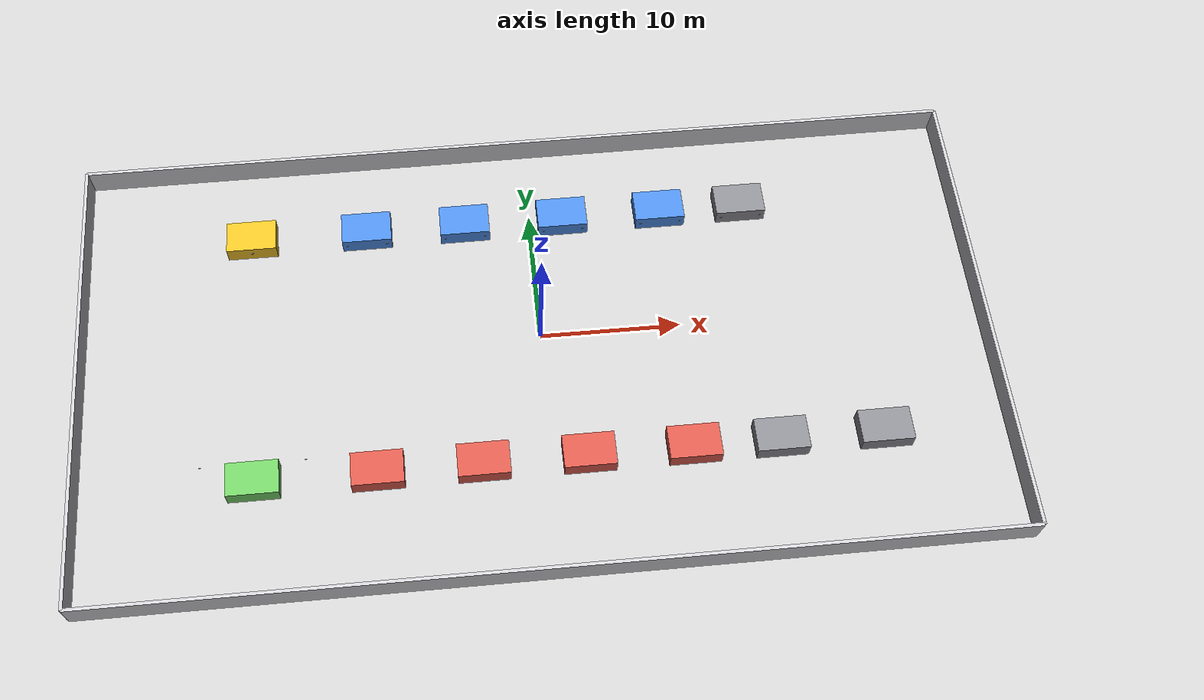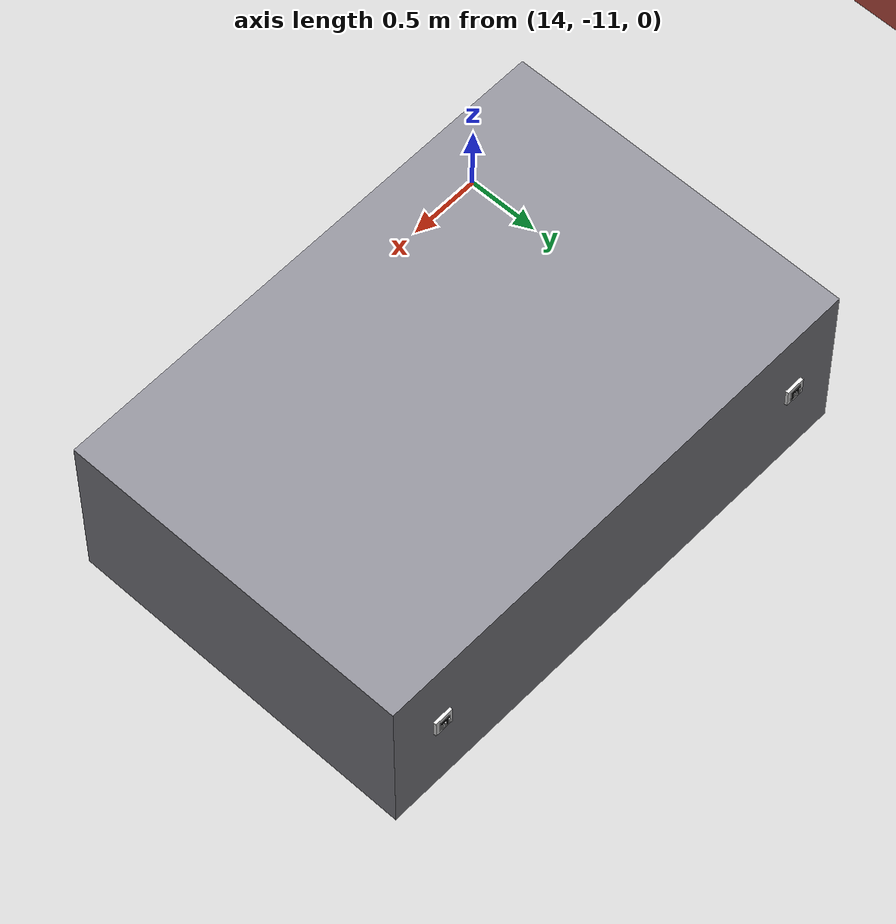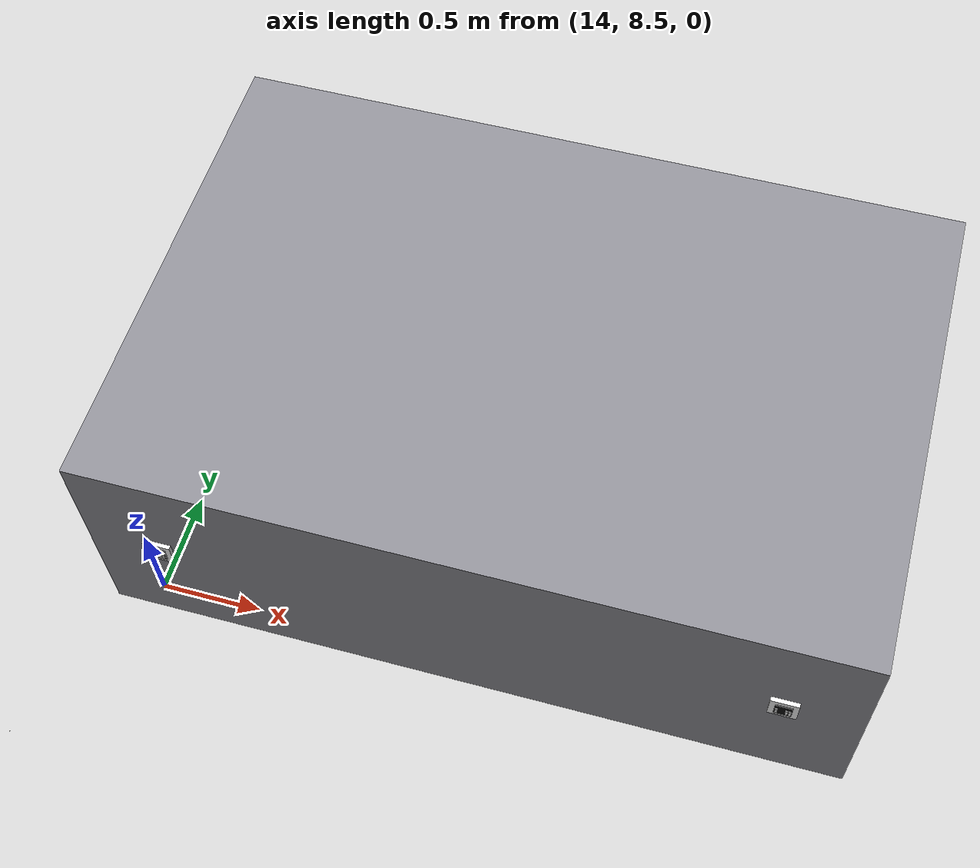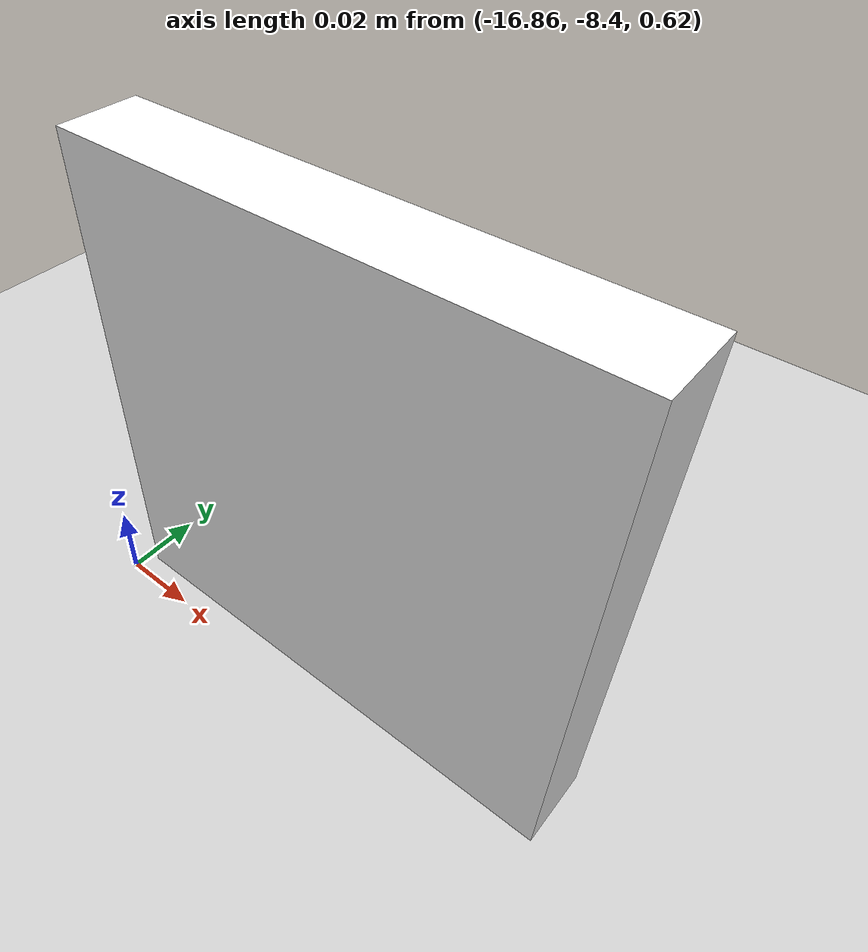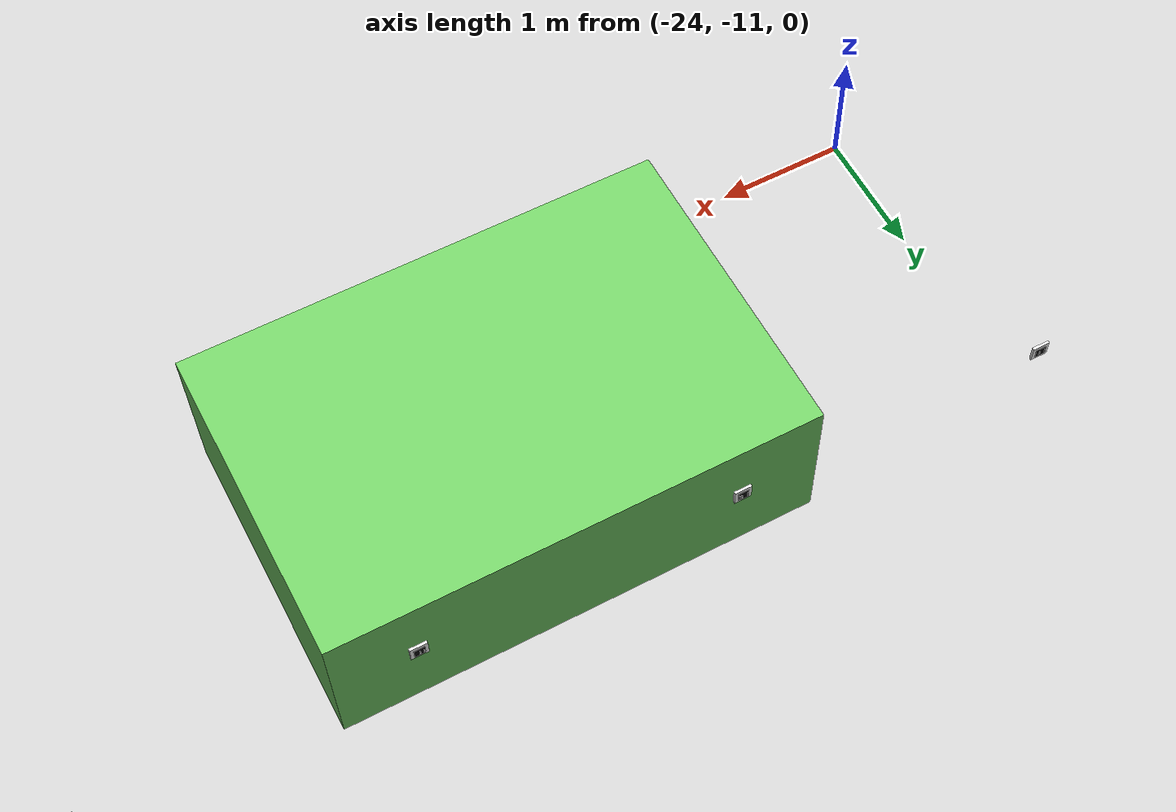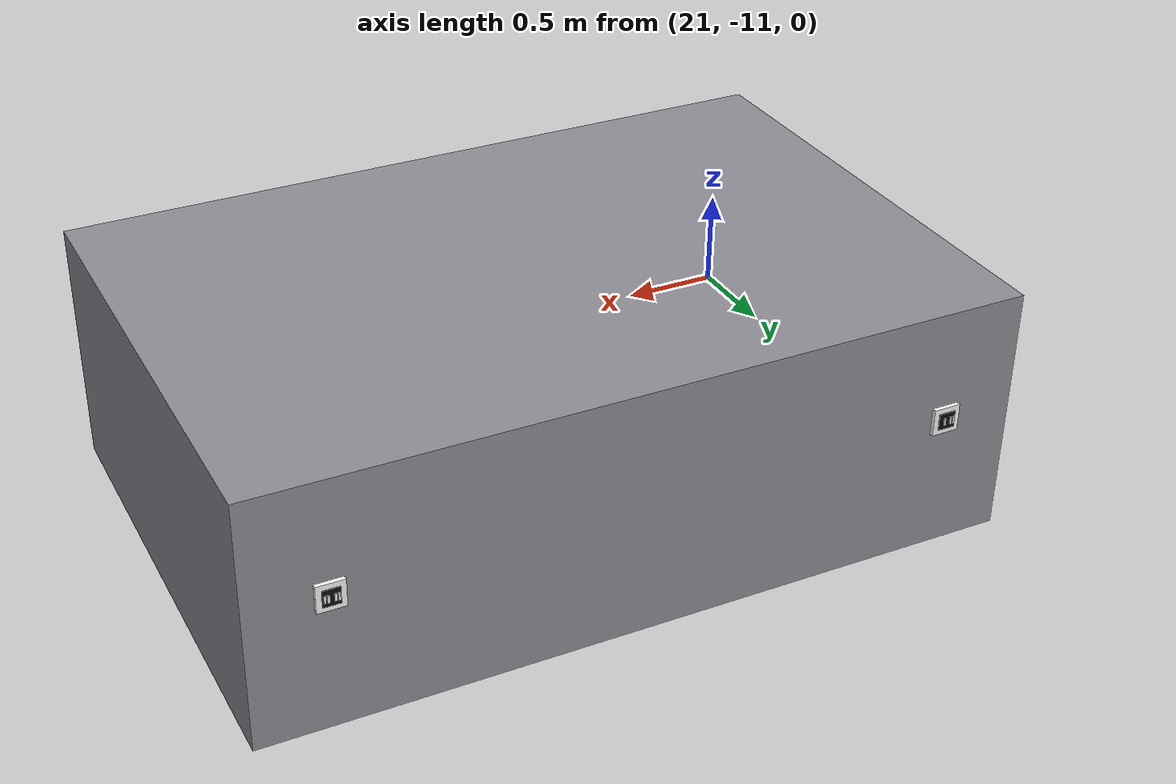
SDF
<?xml version="1.0"?>
<sdf version="1.6">
  <world name="factory">
    <include><uri>model://sun</uri></include>
    <include><uri>model://ground_plane</uri></include>

    <physics type="ode">
      <max_step_size>0.001</max_step_size>
      <real_time_factor>1.0</real_time_factor>
      <real_time_update_rate>1000</real_time_update_rate>
      <ode>
        <solver><type>quick</type><iters>100</iters><sor>1.3</sor></solver>
        <constraints>
          <cfm>0.0</cfm><erp>0.2</erp>
          <contact_max_correcting_vel>100.0</contact_max_correcting_vel>
          <contact_surface_layer>0.001</contact_surface_layer>
        </constraints>
      </ode>
    </physics>

    <scene>
      <ambient>0.6 0.6 0.6 1</ambient>
      <background>0.75 0.80 0.86 1</background>
      <shadows>true</shadows>
    </scene>

    <gui>
      <camera name="user_camera">
        <pose>-14 -22 22 0 0.62 0.9</pose>
      </camera>
    </gui>

    <plugin name="gazebo_ros_state" filename="libgazebo_ros_state.so">
      <ros>
        <namespace>/gazebo</namespace>
      </ros>
      <update_rate>30.0</update_rate>
    </plugin>

    <model name="wall_north">
      <static>true</static>
      <pose>-0.480 15.600 1.000 0 0 0</pose>
      <link name="link">
        <collision name="c"><geometry><box><size>63.840 0.240 2.000</size></box></geometry></collision>
        <visual name="v">
          <geometry><box><size>63.840 0.240 2.000</size></box></geometry>
          <material>
            <ambient>0.8 0.8 0.82 1</ambient>
            <diffuse>0.8 0.8 0.82 1</diffuse>
          </material>
        </visual>
      </link>
    </model>
    <model name="wall_south">
      <static>true</static>
      <pose>-0.480 -18.000 1.000 0 0 0</pose>
      <link name="link">
        <collision name="c"><geometry><box><size>63.840 0.240 2.000</size></box></geometry></collision>
        <visual name="v">
          <geometry><box><size>63.840 0.240 2.000</size></box></geometry>
          <material>
            <ambient>0.8 0.8 0.82 1</ambient>
            <diffuse>0.8 0.8 0.82 1</diffuse>
          </material>
        </visual>
      </link>
    </model>
    <model name="wall_west">
      <static>true</static>
      <pose>-32.400 -1.200 1.000 0 0 0</pose>
      <link name="link">
        <collision name="c"><geometry><box><size>0.240 33.600 2.000</size></box></geometry></collision>
        <visual name="v">
          <geometry><box><size>0.240 33.600 2.000</size></box></geometry>
          <material>
            <ambient>0.8 0.8 0.82 1</ambient>
            <diffuse>0.8 0.8 0.82 1</diffuse>
          </material>
        </visual>
      </link>
    </model>
    <model name="wall_east">
      <static>true</static>
      <pose>31.440 -1.200 1.000 0 0 0</pose>
      <link name="link">
        <collision name="c"><geometry><box><size>0.240 33.600 2.000</size></box></geometry></collision>
        <visual name="v">
          <geometry><box><size>0.240 33.600 2.000</size></box></geometry>
          <material>
            <ambient>0.8 0.8 0.82 1</ambient>
            <diffuse>0.8 0.8 0.82 1</diffuse>
          </material>
        </visual>
      </link>
    </model>
    <model name="overhead_camera">
      <static>true</static>
      <pose>-0.480 -1.200 60.000 0 1.5708 0</pose>
      <link name="link">
        <sensor name="overhead" type="camera">
          <update_rate>4.0</update_rate>
          <camera>
            <horizontal_fov>1.0269</horizontal_fov>
            <image><width>1600</width><height>1000</height><format>R8G8B8</format></image>
            <clip><near>1.0</near><far>70.0</far></clip>
          </camera>
          <plugin name="overhead_camera" filename="libgazebo_ros_camera.so">
            <ros><namespace>/overhead</namespace></ros>
            <camera_name>overhead</camera_name>
            <frame_name>overhead_link</frame_name>
          </plugin>
        </sensor>
      </link>
    </model>

    <model name="m_ASRS">
      <static>true</static>
      <pose>-20.400 9.600 0.600 0 0 0</pose>
      <link name="link">
        <collision name="c"><geometry><box><size>3.600 2.400 1.200</size></box></geometry></collision>
        <visual name="v">
          <geometry><box><size>3.600 2.400 1.200</size></box></geometry>
          <material>
            <ambient>0.95 0.75 0.15 1</ambient>
            <diffuse>0.95 0.75 0.15 1</diffuse>
          </material>
        </visual>
      </link>
    </model>
    <model name="m_GRV1">
      <static>true</static>
      <pose>-12.000 9.600 0.600 0 0 0</pose>
      <link name="link">
        <collision name="c"><geometry><box><size>3.600 2.400 1.200</size></box></geometry></collision>
        <visual name="v">
          <geometry><box><size>3.600 2.400 1.200</size></box></geometry>
          <material>
            <ambient>0.3 0.55 0.9 1</ambient>
            <diffuse>0.3 0.55 0.9 1</diffuse>
          </material>
        </visual>
      </link>
    </model>
    <model name="m_GRV2">
      <static>true</static>
      <pose>-4.800 9.600 0.600 0 0 0</pose>
      <link name="link">
        <collision name="c"><geometry><box><size>3.600 2.400 1.200</size></box></geometry></collision>
        <visual name="v">
          <geometry><box><size>3.600 2.400 1.200</size></box></geometry>
          <material>
            <ambient>0.3 0.55 0.9 1</ambient>
            <diffuse>0.3 0.55 0.9 1</diffuse>
          </material>
        </visual>
      </link>
    </model>
    <model name="m_GRV3">
      <static>true</static>
      <pose>2.400 9.600 0.600 0 0 0</pose>
      <link name="link">
        <collision name="c"><geometry><box><size>3.600 2.400 1.200</size></box></geometry></collision>
        <visual name="v">
          <geometry><box><size>3.600 2.400 1.200</size></box></geometry>
          <material>
            <ambient>0.3 0.55 0.9 1</ambient>
            <diffuse>0.3 0.55 0.9 1</diffuse>
          </material>
        </visual>
      </link>
    </model>
    <model name="m_GRV4">
      <static>true</static>
      <pose>9.600 9.600 0.600 0 0 0</pose>
      <link name="link">
        <collision name="c"><geometry><box><size>3.600 2.400 1.200</size></box></geometry></collision>
        <visual name="v">
          <geometry><box><size>3.600 2.400 1.200</size></box></geometry>
          <material>
            <ambient>0.3 0.55 0.9 1</ambient>
            <diffuse>0.3 0.55 0.9 1</diffuse>
          </material>
        </visual>
      </link>
    </model>
    <model name="m_CTR1">
      <static>true</static>
      <pose>-12.000 -9.600 0.600 0 0 0</pose>
      <link name="link">
        <collision name="c"><geometry><box><size>3.600 2.400 1.200</size></box></geometry></collision>
        <visual name="v">
          <geometry><box><size>3.600 2.400 1.200</size></box></geometry>
          <material>
            <ambient>0.85 0.35 0.3 1</ambient>
            <diffuse>0.85 0.35 0.3 1</diffuse>
          </material>
        </visual>
      </link>
    </model>
    <model name="m_CTR2">
      <static>true</static>
      <pose>-4.800 -9.600 0.600 0 0 0</pose>
      <link name="link">
        <collision name="c"><geometry><box><size>3.600 2.400 1.200</size></box></geometry></collision>
        <visual name="v">
          <geometry><box><size>3.600 2.400 1.200</size></box></geometry>
          <material>
            <ambient>0.85 0.35 0.3 1</ambient>
            <diffuse>0.85 0.35 0.3 1</diffuse>
          </material>
        </visual>
      </link>
    </model>
    <model name="m_CTR3">
      <static>true</static>
      <pose>2.400 -9.600 0.600 0 0 0</pose>
      <link name="link">
        <collision name="c"><geometry><box><size>3.600 2.400 1.200</size></box></geometry></collision>
        <visual name="v">
          <geometry><box><size>3.600 2.400 1.200</size></box></geometry>
          <material>
            <ambient>0.85 0.35 0.3 1</ambient>
            <diffuse>0.85 0.35 0.3 1</diffuse>
          </material>
        </visual>
      </link>
    </model>
    <model name="m_CTR4">
      <static>true</static>
      <pose>9.600 -9.600 0.600 0 0 0</pose>
      <link name="link">
        <collision name="c"><geometry><box><size>3.600 2.400 1.200</size></box></geometry></collision>
        <visual name="v">
          <geometry><box><size>3.600 2.400 1.200</size></box></geometry>
          <material>
            <ambient>0.85 0.35 0.3 1</ambient>
            <diffuse>0.85 0.35 0.3 1</diffuse>
          </material>
        </visual>
      </link>
    </model>
    <model name="m_SLT">
      <static>true</static>
      <pose>-20.400 -9.600 0.600 0 0 0</pose>
      <link name="link">
        <collision name="c"><geometry><box><size>3.600 2.400 1.200</size></box></geometry></collision>
        <visual name="v">
          <geometry><box><size>3.600 2.400 1.200</size></box></geometry>
          <material>
            <ambient>0.45 0.8 0.4 1</ambient>
            <diffuse>0.45 0.8 0.4 1</diffuse>
          </material>
        </visual>
      </link>
    </model>
    <model name="m_WIP_GRV">
      <static>true</static>
      <pose>15.600 9.600 0.600 0 0 0</pose>
      <link name="link">
        <collision name="c"><geometry><box><size>3.600 2.400 1.200</size></box></geometry></collision>
        <visual name="v">
          <geometry><box><size>3.600 2.400 1.200</size></box></geometry>
          <material>
            <ambient>0.55 0.55 0.58 1</ambient>
            <diffuse>0.55 0.55 0.58 1</diffuse>
          </material>
        </visual>
      </link>
    </model>
    <model name="m_WIP_CTR">
      <static>true</static>
      <pose>15.600 -9.600 0.600 0 0 0</pose>
      <link name="link">
        <collision name="c"><geometry><box><size>3.600 2.400 1.200</size></box></geometry></collision>
        <visual name="v">
          <geometry><box><size>3.600 2.400 1.200</size></box></geometry>
          <material>
            <ambient>0.55 0.55 0.58 1</ambient>
            <diffuse>0.55 0.55 0.58 1</diffuse>
          </material>
        </visual>
      </link>
    </model>
    <model name="m_WIP_SLT">
      <static>true</static>
      <pose>22.800 -9.600 0.600 0 0 0</pose>
      <link name="link">
        <collision name="c"><geometry><box><size>3.600 2.400 1.200</size></box></geometry></collision>
        <visual name="v">
          <geometry><box><size>3.600 2.400 1.200</size></box></geometry>
          <material>
            <ambient>0.55 0.55 0.58 1</ambient>
            <diffuse>0.55 0.55 0.58 1</diffuse>
          </material>
        </visual>
      </link>
    </model>
    <model name="marker_ASRS">
      <static>true</static>
      <pose>-20.400 8.380 0.675 0 0 0</pose>
      <link name="link">
        <visual name="v">
          <geometry><box><size>0.130 0.020 0.130</size></box></geometry>
          <material>
            <ambient>0.97 0.97 0.97 1</ambient>
            <diffuse>0.97 0.97 0.97 1</diffuse>
          </material>
        </visual>
      </link>
    </model>
    <model name="markerdot_ASRS">
      <static>true</static>
      <pose>-20.400 8.370 0.675 0 0 0</pose>
      <link name="link">
        <visual name="v">
          <geometry><box><size>0.080 0.010 0.080</size></box></geometry>
          <material>
            <ambient>0.05 0.05 0.05 1</ambient>
            <diffuse>0.05 0.05 0.05 1</diffuse>
          </material>
        </visual>
      </link>
    </model>
    <model name="markerbit_ASRS_0">
      <static>true</static>
      <pose>-20.430 8.360 0.675 0 0 0</pose>
      <link name="link">
        <visual name="v">
          <geometry><box><size>0.009 0.005 0.034</size></box></geometry>
          <material>
            <ambient>0.97 0.97 0.97 1</ambient>
            <diffuse>0.97 0.97 0.97 1</diffuse>
          </material>
        </visual>
      </link>
    </model>
    <model name="marker_GRV1_LD">
      <static>true</static>
      <pose>-13.440 8.380 0.675 0 0 0</pose>
      <link name="link">
        <visual name="v">
          <geometry><box><size>0.130 0.020 0.130</size></box></geometry>
          <material>
            <ambient>0.97 0.97 0.97 1</ambient>
            <diffuse>0.97 0.97 0.97 1</diffuse>
          </material>
        </visual>
      </link>
    </model>
    <model name="markerdot_GRV1_LD">
      <static>true</static>
      <pose>-13.440 8.370 0.675 0 0 0</pose>
      <link name="link">
        <visual name="v">
          <geometry><box><size>0.080 0.010 0.080</size></box></geometry>
          <material>
            <ambient>0.05 0.05 0.05 1</ambient>
            <diffuse>0.05 0.05 0.05 1</diffuse>
          </material>
        </visual>
      </link>
    </model>
    <model name="markerbit_GRV1_LD_1">
      <static>true</static>
      <pose>-13.455 8.360 0.675 0 0 0</pose>
      <link name="link">
        <visual name="v">
          <geometry><box><size>0.009 0.005 0.034</size></box></geometry>
          <material>
            <ambient>0.97 0.97 0.97 1</ambient>
            <diffuse>0.97 0.97 0.97 1</diffuse>
          </material>
        </visual>
      </link>
    </model>
    <model name="markerbit_GRV1_LD_3">
      <static>true</static>
      <pose>-13.425 8.360 0.675 0 0 0</pose>
      <link name="link">
        <visual name="v">
          <geometry><box><size>0.009 0.005 0.034</size></box></geometry>
          <material>
            <ambient>0.97 0.97 0.97 1</ambient>
            <diffuse>0.97 0.97 0.97 1</diffuse>
          </material>
        </visual>
      </link>
    </model>
    <model name="marker_GRV1_ULD">
      <static>true</static>
      <pose>-10.560 8.380 0.675 0 0 0</pose>
      <link name="link">
        <visual name="v">
          <geometry><box><size>0.130 0.020 0.130</size></box></geometry>
          <material>
            <ambient>0.97 0.97 0.97 1</ambient>
            <diffuse>0.97 0.97 0.97 1</diffuse>
          </material>
        </visual>
      </link>
    </model>
    <model name="markerdot_GRV1_ULD">
      <static>true</static>
      <pose>-10.560 8.370 0.675 0 0 0</pose>
      <link name="link">
        <visual name="v">
          <geometry><box><size>0.080 0.010 0.080</size></box></geometry>
          <material>
            <ambient>0.05 0.05 0.05 1</ambient>
            <diffuse>0.05 0.05 0.05 1</diffuse>
          </material>
        </visual>
      </link>
    </model>
    <model name="markerbit_GRV1_ULD_0">
      <static>true</static>
      <pose>-10.590 8.360 0.675 0 0 0</pose>
      <link name="link">
        <visual name="v">
          <geometry><box><size>0.009 0.005 0.034</size></box></geometry>
          <material>
            <ambient>0.97 0.97 0.97 1</ambient>
            <diffuse>0.97 0.97 0.97 1</diffuse>
          </material>
        </visual>
      </link>
    </model>
    <model name="markerbit_GRV1_ULD_1">
      <static>true</static>
      <pose>-10.575 8.360 0.675 0 0 0</pose>
      <link name="link">
        <visual name="v">
          <geometry><box><size>0.009 0.005 0.034</size></box></geometry>
          <material>
            <ambient>0.97 0.97 0.97 1</ambient>
            <diffuse>0.97 0.97 0.97 1</diffuse>
          </material>
        </visual>
      </link>
    </model>
    <model name="markerbit_GRV1_ULD_3">
      <static>true</static>
      <pose>-10.545 8.360 0.675 0 0 0</pose>
      <link name="link">
        <visual name="v">
          <geometry><box><size>0.009 0.005 0.034</size></box></geometry>
          <material>
            <ambient>0.97 0.97 0.97 1</ambient>
            <diffuse>0.97 0.97 0.97 1</diffuse>
          </material>
        </visual>
      </link>
    </model>
    <model name="marker_GRV2_LD">
      <static>true</static>
      <pose>-6.240 8.380 0.675 0 0 0</pose>
      <link name="link">
        <visual name="v">
          <geometry><box><size>0.130 0.020 0.130</size></box></geometry>
          <material>
            <ambient>0.97 0.97 0.97 1</ambient>
            <diffuse>0.97 0.97 0.97 1</diffuse>
          </material>
        </visual>
      </link>
    </model>
    <model name="markerdot_GRV2_LD">
      <static>true</static>
      <pose>-6.240 8.370 0.675 0 0 0</pose>
      <link name="link">
        <visual name="v">
          <geometry><box><size>0.080 0.010 0.080</size></box></geometry>
          <material>
            <ambient>0.05 0.05 0.05 1</ambient>
            <diffuse>0.05 0.05 0.05 1</diffuse>
          </material>
        </visual>
      </link>
    </model>
    <model name="markerbit_GRV2_LD_2">
      <static>true</static>
      <pose>-6.240 8.360 0.675 0 0 0</pose>
      <link name="link">
        <visual name="v">
          <geometry><box><size>0.009 0.005 0.034</size></box></geometry>
          <material>
            <ambient>0.97 0.97 0.97 1</ambient>
            <diffuse>0.97 0.97 0.97 1</diffuse>
          </material>
        </visual>
      </link>
    </model>
    <model name="markerbit_GRV2_LD_3">
      <static>true</static>
      <pose>-6.225 8.360 0.675 0 0 0</pose>
      <link name="link">
        <visual name="v">
          <geometry><box><size>0.009 0.005 0.034</size></box></geometry>
          <material>
            <ambient>0.97 0.97 0.97 1</ambient>
            <diffuse>0.97 0.97 0.97 1</diffuse>
          </material>
        </visual>
      </link>
    </model>
    <model name="marker_GRV2_ULD">
      <static>true</static>
      <pose>-3.360 8.380 0.675 0 0 0</pose>
      <link name="link">
        <visual name="v">
          <geometry><box><size>0.130 0.020 0.130</size></box></geometry>
          <material>
            <ambient>0.97 0.97 0.97 1</ambient>
            <diffuse>0.97 0.97 0.97 1</diffuse>
          </material>
        </visual>
      </link>
    </model>
    <model name="markerdot_GRV2_ULD">
      <static>true</static>
      <pose>-3.360 8.370 0.675 0 0 0</pose>
      <link name="link">
        <visual name="v">
          <geometry><box><size>0.080 0.010 0.080</size></box></geometry>
          <material>
            <ambient>0.05 0.05 0.05 1</ambient>
            <diffuse>0.05 0.05 0.05 1</diffuse>
          </material>
        </visual>
      </link>
    </model>
    <model name="markerbit_GRV2_ULD_0">
      <static>true</static>
      <pose>-3.390 8.360 0.675 0 0 0</pose>
      <link name="link">
        <visual name="v">
          <geometry><box><size>0.009 0.005 0.034</size></box></geometry>
          <material>
            <ambient>0.97 0.97 0.97 1</ambient>
            <diffuse>0.97 0.97 0.97 1</diffuse>
          </material>
        </visual>
      </link>
    </model>
    <model name="markerbit_GRV2_ULD_2">
      <static>true</static>
      <pose>-3.360 8.360 0.675 0 0 0</pose>
      <link name="link">
        <visual name="v">
          <geometry><box><size>0.009 0.005 0.034</size></box></geometry>
          <material>
            <ambient>0.97 0.97 0.97 1</ambient>
            <diffuse>0.97 0.97 0.97 1</diffuse>
          </material>
        </visual>
      </link>
    </model>
    <model name="markerbit_GRV2_ULD_3">
      <static>true</static>
      <pose>-3.345 8.360 0.675 0 0 0</pose>
      <link name="link">
        <visual name="v">
          <geometry><box><size>0.009 0.005 0.034</size></box></geometry>
          <material>
            <ambient>0.97 0.97 0.97 1</ambient>
            <diffuse>0.97 0.97 0.97 1</diffuse>
          </material>
        </visual>
      </link>
    </model>
    <model name="marker_GRV3_LD">
      <static>true</static>
      <pose>0.960 8.380 0.675 0 0 0</pose>
      <link name="link">
        <visual name="v">
          <geometry><box><size>0.130 0.020 0.130</size></box></geometry>
          <material>
            <ambient>0.97 0.97 0.97 1</ambient>
            <diffuse>0.97 0.97 0.97 1</diffuse>
          </material>
        </visual>
      </link>
    </model>
    <model name="markerdot_GRV3_LD">
      <static>true</static>
      <pose>0.960 8.370 0.675 0 0 0</pose>
      <link name="link">
        <visual name="v">
          <geometry><box><size>0.080 0.010 0.080</size></box></geometry>
          <material>
            <ambient>0.05 0.05 0.05 1</ambient>
            <diffuse>0.05 0.05 0.05 1</diffuse>
          </material>
        </visual>
      </link>
    </model>
    <model name="markerbit_GRV3_LD_1">
      <static>true</static>
      <pose>0.945 8.360 0.675 0 0 0</pose>
      <link name="link">
        <visual name="v">
          <geometry><box><size>0.009 0.005 0.034</size></box></geometry>
          <material>
            <ambient>0.97 0.97 0.97 1</ambient>
            <diffuse>0.97 0.97 0.97 1</diffuse>
          </material>
        </visual>
      </link>
    </model>
    <model name="markerbit_GRV3_LD_2">
      <static>true</static>
      <pose>0.960 8.360 0.675 0 0 0</pose>
      <link name="link">
        <visual name="v">
          <geometry><box><size>0.009 0.005 0.034</size></box></geometry>
          <material>
            <ambient>0.97 0.97 0.97 1</ambient>
            <diffuse>0.97 0.97 0.97 1</diffuse>
          </material>
        </visual>
      </link>
    </model>
    <model name="markerbit_GRV3_LD_3">
      <static>true</static>
      <pose>0.975 8.360 0.675 0 0 0</pose>
      <link name="link">
        <visual name="v">
          <geometry><box><size>0.009 0.005 0.034</size></box></geometry>
          <material>
            <ambient>0.97 0.97 0.97 1</ambient>
            <diffuse>0.97 0.97 0.97 1</diffuse>
          </material>
        </visual>
      </link>
    </model>
    <model name="marker_GRV3_ULD">
      <static>true</static>
      <pose>3.840 8.380 0.675 0 0 0</pose>
      <link name="link">
        <visual name="v">
          <geometry><box><size>0.130 0.020 0.130</size></box></geometry>
          <material>
            <ambient>0.97 0.97 0.97 1</ambient>
            <diffuse>0.97 0.97 0.97 1</diffuse>
          </material>
        </visual>
      </link>
    </model>
    <model name="markerdot_GRV3_ULD">
      <static>true</static>
      <pose>3.840 8.370 0.675 0 0 0</pose>
      <link name="link">
        <visual name="v">
          <geometry><box><size>0.080 0.010 0.080</size></box></geometry>
          <material>
            <ambient>0.05 0.05 0.05 1</ambient>
            <diffuse>0.05 0.05 0.05 1</diffuse>
          </material>
        </visual>
      </link>
    </model>
    <model name="markerbit_GRV3_ULD_0">
      <static>true</static>
      <pose>3.810 8.360 0.675 0 0 0</pose>
      <link name="link">
        <visual name="v">
          <geometry><box><size>0.009 0.005 0.034</size></box></geometry>
          <material>
            <ambient>0.97 0.97 0.97 1</ambient>
            <diffuse>0.97 0.97 0.97 1</diffuse>
          </material>
        </visual>
      </link>
    </model>
    <model name="markerbit_GRV3_ULD_1">
      <static>true</static>
      <pose>3.825 8.360 0.675 0 0 0</pose>
      <link name="link">
        <visual name="v">
          <geometry><box><size>0.009 0.005 0.034</size></box></geometry>
          <material>
            <ambient>0.97 0.97 0.97 1</ambient>
            <diffuse>0.97 0.97 0.97 1</diffuse>
          </material>
        </visual>
      </link>
    </model>
    <model name="markerbit_GRV3_ULD_2">
      <static>true</static>
      <pose>3.840 8.360 0.675 0 0 0</pose>
      <link name="link">
        <visual name="v">
          <geometry><box><size>0.009 0.005 0.034</size></box></geometry>
          <material>
            <ambient>0.97 0.97 0.97 1</ambient>
            <diffuse>0.97 0.97 0.97 1</diffuse>
          </material>
        </visual>
      </link>
    </model>
    <model name="markerbit_GRV3_ULD_3">
      <static>true</static>
      <pose>3.855 8.360 0.675 0 0 0</pose>
      <link name="link">
        <visual name="v">
          <geometry><box><size>0.009 0.005 0.034</size></box></geometry>
          <material>
            <ambient>0.97 0.97 0.97 1</ambient>
            <diffuse>0.97 0.97 0.97 1</diffuse>
          </material>
        </visual>
      </link>
    </model>
    <model name="marker_GRV4_LD">
      <static>true</static>
      <pose>8.160 8.380 0.675 0 0 0</pose>
      <link name="link">
        <visual name="v">
          <geometry><box><size>0.130 0.020 0.130</size></box></geometry>
          <material>
            <ambient>0.97 0.97 0.97 1</ambient>
            <diffuse>0.97 0.97 0.97 1</diffuse>
          </material>
        </visual>
      </link>
    </model>
    <model name="markerdot_GRV4_LD">
      <static>true</static>
      <pose>8.160 8.370 0.675 0 0 0</pose>
      <link name="link">
        <visual name="v">
          <geometry><box><size>0.080 0.010 0.080</size></box></geometry>
          <material>
            <ambient>0.05 0.05 0.05 1</ambient>
            <diffuse>0.05 0.05 0.05 1</diffuse>
          </material>
        </visual>
      </link>
    </model>
    <model name="markerbit_GRV4_LD_4">
      <static>true</static>
      <pose>8.190 8.360 0.675 0 0 0</pose>
      <link name="link">
        <visual name="v">
          <geometry><box><size>0.009 0.005 0.034</size></box></geometry>
          <material>
            <ambient>0.97 0.97 0.97 1</ambient>
            <diffuse>0.97 0.97 0.97 1</diffuse>
          </material>
        </visual>
      </link>
    </model>
    <model name="marker_GRV4_ULD">
      <static>true</static>
      <pose>11.040 8.380 0.675 0 0 0</pose>
      <link name="link">
        <visual name="v">
          <geometry><box><size>0.130 0.020 0.130</size></box></geometry>
          <material>
            <ambient>0.97 0.97 0.97 1</ambient>
            <diffuse>0.97 0.97 0.97 1</diffuse>
          </material>
        </visual>
      </link>
    </model>
    <model name="markerdot_GRV4_ULD">
      <static>true</static>
      <pose>11.040 8.370 0.675 0 0 0</pose>
      <link name="link">
        <visual name="v">
          <geometry><box><size>0.080 0.010 0.080</size></box></geometry>
          <material>
            <ambient>0.05 0.05 0.05 1</ambient>
            <diffuse>0.05 0.05 0.05 1</diffuse>
          </material>
        </visual>
      </link>
    </model>
    <model name="markerbit_GRV4_ULD_0">
      <static>true</static>
      <pose>11.010 8.360 0.675 0 0 0</pose>
      <link name="link">
        <visual name="v">
          <geometry><box><size>0.009 0.005 0.034</size></box></geometry>
          <material>
            <ambient>0.97 0.97 0.97 1</ambient>
            <diffuse>0.97 0.97 0.97 1</diffuse>
          </material>
        </visual>
      </link>
    </model>
    <model name="markerbit_GRV4_ULD_4">
      <static>true</static>
      <pose>11.070 8.360 0.675 0 0 0</pose>
      <link name="link">
        <visual name="v">
          <geometry><box><size>0.009 0.005 0.034</size></box></geometry>
          <material>
            <ambient>0.97 0.97 0.97 1</ambient>
            <diffuse>0.97 0.97 0.97 1</diffuse>
          </material>
        </visual>
      </link>
    </model>
    <model name="marker_CTR1_LD">
      <static>true</static>
      <pose>-13.440 -8.380 0.675 0 0 0</pose>
      <link name="link">
        <visual name="v">
          <geometry><box><size>0.130 0.020 0.130</size></box></geometry>
          <material>
            <ambient>0.97 0.97 0.97 1</ambient>
            <diffuse>0.97 0.97 0.97 1</diffuse>
          </material>
        </visual>
      </link>
    </model>
    <model name="markerdot_CTR1_LD">
      <static>true</static>
      <pose>-13.440 -8.370 0.675 0 0 0</pose>
      <link name="link">
        <visual name="v">
          <geometry><box><size>0.080 0.010 0.080</size></box></geometry>
          <material>
            <ambient>0.05 0.05 0.05 1</ambient>
            <diffuse>0.05 0.05 0.05 1</diffuse>
          </material>
        </visual>
      </link>
    </model>
    <model name="markerbit_CTR1_LD_1">
      <static>true</static>
      <pose>-13.425 -8.360 0.675 0 0 0</pose>
      <link name="link">
        <visual name="v">
          <geometry><box><size>0.009 0.005 0.034</size></box></geometry>
          <material>
            <ambient>0.97 0.97 0.97 1</ambient>
            <diffuse>0.97 0.97 0.97 1</diffuse>
          </material>
        </visual>
      </link>
    </model>
    <model name="marker_CTR1_ULD">
      <static>true</static>
      <pose>-10.560 -8.380 0.675 0 0 0</pose>
      <link name="link">
        <visual name="v">
          <geometry><box><size>0.130 0.020 0.130</size></box></geometry>
          <material>
            <ambient>0.97 0.97 0.97 1</ambient>
            <diffuse>0.97 0.97 0.97 1</diffuse>
          </material>
        </visual>
      </link>
    </model>
    <model name="markerdot_CTR1_ULD">
      <static>true</static>
      <pose>-10.560 -8.370 0.675 0 0 0</pose>
      <link name="link">
        <visual name="v">
          <geometry><box><size>0.080 0.010 0.080</size></box></geometry>
          <material>
            <ambient>0.05 0.05 0.05 1</ambient>
            <diffuse>0.05 0.05 0.05 1</diffuse>
          </material>
        </visual>
      </link>
    </model>
    <model name="markerbit_CTR1_ULD_0">
      <static>true</static>
      <pose>-10.530 -8.360 0.675 0 0 0</pose>
      <link name="link">
        <visual name="v">
          <geometry><box><size>0.009 0.005 0.034</size></box></geometry>
          <material>
            <ambient>0.97 0.97 0.97 1</ambient>
            <diffuse>0.97 0.97 0.97 1</diffuse>
          </material>
        </visual>
      </link>
    </model>
    <model name="markerbit_CTR1_ULD_1">
      <static>true</static>
      <pose>-10.545 -8.360 0.675 0 0 0</pose>
      <link name="link">
        <visual name="v">
          <geometry><box><size>0.009 0.005 0.034</size></box></geometry>
          <material>
            <ambient>0.97 0.97 0.97 1</ambient>
            <diffuse>0.97 0.97 0.97 1</diffuse>
          </material>
        </visual>
      </link>
    </model>
    <model name="marker_CTR2_LD">
      <static>true</static>
      <pose>-6.240 -8.380 0.675 0 0 0</pose>
      <link name="link">
        <visual name="v">
          <geometry><box><size>0.130 0.020 0.130</size></box></geometry>
          <material>
            <ambient>0.97 0.97 0.97 1</ambient>
            <diffuse>0.97 0.97 0.97 1</diffuse>
          </material>
        </visual>
      </link>
    </model>
    <model name="markerdot_CTR2_LD">
      <static>true</static>
      <pose>-6.240 -8.370 0.675 0 0 0</pose>
      <link name="link">
        <visual name="v">
          <geometry><box><size>0.080 0.010 0.080</size></box></geometry>
          <material>
            <ambient>0.05 0.05 0.05 1</ambient>
            <diffuse>0.05 0.05 0.05 1</diffuse>
          </material>
        </visual>
      </link>
    </model>
    <model name="markerbit_CTR2_LD_2">
      <static>true</static>
      <pose>-6.240 -8.360 0.675 0 0 0</pose>
      <link name="link">
        <visual name="v">
          <geometry><box><size>0.009 0.005 0.034</size></box></geometry>
          <material>
            <ambient>0.97 0.97 0.97 1</ambient>
            <diffuse>0.97 0.97 0.97 1</diffuse>
          </material>
        </visual>
      </link>
    </model>
    <model name="marker_CTR2_ULD">
      <static>true</static>
      <pose>-3.360 -8.380 0.675 0 0 0</pose>
      <link name="link">
        <visual name="v">
          <geometry><box><size>0.130 0.020 0.130</size></box></geometry>
          <material>
            <ambient>0.97 0.97 0.97 1</ambient>
            <diffuse>0.97 0.97 0.97 1</diffuse>
          </material>
        </visual>
      </link>
    </model>
    <model name="markerdot_CTR2_ULD">
      <static>true</static>
      <pose>-3.360 -8.370 0.675 0 0 0</pose>
      <link name="link">
        <visual name="v">
          <geometry><box><size>0.080 0.010 0.080</size></box></geometry>
          <material>
            <ambient>0.05 0.05 0.05 1</ambient>
            <diffuse>0.05 0.05 0.05 1</diffuse>
          </material>
        </visual>
      </link>
    </model>
    <model name="markerbit_CTR2_ULD_0">
      <static>true</static>
      <pose>-3.330 -8.360 0.675 0 0 0</pose>
      <link name="link">
        <visual name="v">
          <geometry><box><size>0.009 0.005 0.034</size></box></geometry>
          <material>
            <ambient>0.97 0.97 0.97 1</ambient>
            <diffuse>0.97 0.97 0.97 1</diffuse>
          </material>
        </visual>
      </link>
    </model>
    <model name="markerbit_CTR2_ULD_2">
      <static>true</static>
      <pose>-3.360 -8.360 0.675 0 0 0</pose>
      <link name="link">
        <visual name="v">
          <geometry><box><size>0.009 0.005 0.034</size></box></geometry>
          <material>
            <ambient>0.97 0.97 0.97 1</ambient>
            <diffuse>0.97 0.97 0.97 1</diffuse>
          </material>
        </visual>
      </link>
    </model>
    <model name="marker_CTR3_LD">
      <static>true</static>
      <pose>0.960 -8.380 0.675 0 0 0</pose>
      <link name="link">
        <visual name="v">
          <geometry><box><size>0.130 0.020 0.130</size></box></geometry>
          <material>
            <ambient>0.97 0.97 0.97 1</ambient>
            <diffuse>0.97 0.97 0.97 1</diffuse>
          </material>
        </visual>
      </link>
    </model>
    <model name="markerdot_CTR3_LD">
      <static>true</static>
      <pose>0.960 -8.370 0.675 0 0 0</pose>
      <link name="link">
        <visual name="v">
          <geometry><box><size>0.080 0.010 0.080</size></box></geometry>
          <material>
            <ambient>0.05 0.05 0.05 1</ambient>
            <diffuse>0.05 0.05 0.05 1</diffuse>
          </material>
        </visual>
      </link>
    </model>
    <model name="markerbit_CTR3_LD_1">
      <static>true</static>
      <pose>0.975 -8.360 0.675 0 0 0</pose>
      <link name="link">
        <visual name="v">
          <geometry><box><size>0.009 0.005 0.034</size></box></geometry>
          <material>
            <ambient>0.97 0.97 0.97 1</ambient>
            <diffuse>0.97 0.97 0.97 1</diffuse>
          </material>
        </visual>
      </link>
    </model>
    <model name="markerbit_CTR3_LD_2">
      <static>true</static>
      <pose>0.960 -8.360 0.675 0 0 0</pose>
      <link name="link">
        <visual name="v">
          <geometry><box><size>0.009 0.005 0.034</size></box></geometry>
          <material>
            <ambient>0.97 0.97 0.97 1</ambient>
            <diffuse>0.97 0.97 0.97 1</diffuse>
          </material>
        </visual>
      </link>
    </model>
    <model name="marker_CTR3_ULD">
      <static>true</static>
      <pose>3.840 -8.380 0.675 0 0 0</pose>
      <link name="link">
        <visual name="v">
          <geometry><box><size>0.130 0.020 0.130</size></box></geometry>
          <material>
            <ambient>0.97 0.97 0.97 1</ambient>
            <diffuse>0.97 0.97 0.97 1</diffuse>
          </material>
        </visual>
      </link>
    </model>
    <model name="markerdot_CTR3_ULD">
      <static>true</static>
      <pose>3.840 -8.370 0.675 0 0 0</pose>
      <link name="link">
        <visual name="v">
          <geometry><box><size>0.080 0.010 0.080</size></box></geometry>
          <material>
            <ambient>0.05 0.05 0.05 1</ambient>
            <diffuse>0.05 0.05 0.05 1</diffuse>
          </material>
        </visual>
      </link>
    </model>
    <model name="markerbit_CTR3_ULD_0">
      <static>true</static>
      <pose>3.870 -8.360 0.675 0 0 0</pose>
      <link name="link">
        <visual name="v">
          <geometry><box><size>0.009 0.005 0.034</size></box></geometry>
          <material>
            <ambient>0.97 0.97 0.97 1</ambient>
            <diffuse>0.97 0.97 0.97 1</diffuse>
          </material>
        </visual>
      </link>
    </model>
    <model name="markerbit_CTR3_ULD_1">
      <static>true</static>
      <pose>3.855 -8.360 0.675 0 0 0</pose>
      <link name="link">
        <visual name="v">
          <geometry><box><size>0.009 0.005 0.034</size></box></geometry>
          <material>
            <ambient>0.97 0.97 0.97 1</ambient>
            <diffuse>0.97 0.97 0.97 1</diffuse>
          </material>
        </visual>
      </link>
    </model>
    <model name="markerbit_CTR3_ULD_2">
      <static>true</static>
      <pose>3.840 -8.360 0.675 0 0 0</pose>
      <link name="link">
        <visual name="v">
          <geometry><box><size>0.009 0.005 0.034</size></box></geometry>
          <material>
            <ambient>0.97 0.97 0.97 1</ambient>
            <diffuse>0.97 0.97 0.97 1</diffuse>
          </material>
        </visual>
      </link>
    </model>
    <model name="marker_CTR4_LD">
      <static>true</static>
      <pose>8.160 -8.380 0.675 0 0 0</pose>
      <link name="link">
        <visual name="v">
          <geometry><box><size>0.130 0.020 0.130</size></box></geometry>
          <material>
            <ambient>0.97 0.97 0.97 1</ambient>
            <diffuse>0.97 0.97 0.97 1</diffuse>
          </material>
        </visual>
      </link>
    </model>
    <model name="markerdot_CTR4_LD">
      <static>true</static>
      <pose>8.160 -8.370 0.675 0 0 0</pose>
      <link name="link">
        <visual name="v">
          <geometry><box><size>0.080 0.010 0.080</size></box></geometry>
          <material>
            <ambient>0.05 0.05 0.05 1</ambient>
            <diffuse>0.05 0.05 0.05 1</diffuse>
          </material>
        </visual>
      </link>
    </model>
    <model name="markerbit_CTR4_LD_3">
      <static>true</static>
      <pose>8.145 -8.360 0.675 0 0 0</pose>
      <link name="link">
        <visual name="v">
          <geometry><box><size>0.009 0.005 0.034</size></box></geometry>
          <material>
            <ambient>0.97 0.97 0.97 1</ambient>
            <diffuse>0.97 0.97 0.97 1</diffuse>
          </material>
        </visual>
      </link>
    </model>
    <model name="marker_CTR4_ULD">
      <static>true</static>
      <pose>11.040 -8.380 0.675 0 0 0</pose>
      <link name="link">
        <visual name="v">
          <geometry><box><size>0.130 0.020 0.130</size></box></geometry>
          <material>
            <ambient>0.97 0.97 0.97 1</ambient>
            <diffuse>0.97 0.97 0.97 1</diffuse>
          </material>
        </visual>
      </link>
    </model>
    <model name="markerdot_CTR4_ULD">
      <static>true</static>
      <pose>11.040 -8.370 0.675 0 0 0</pose>
      <link name="link">
        <visual name="v">
          <geometry><box><size>0.080 0.010 0.080</size></box></geometry>
          <material>
            <ambient>0.05 0.05 0.05 1</ambient>
            <diffuse>0.05 0.05 0.05 1</diffuse>
          </material>
        </visual>
      </link>
    </model>
    <model name="markerbit_CTR4_ULD_0">
      <static>true</static>
      <pose>11.070 -8.360 0.675 0 0 0</pose>
      <link name="link">
        <visual name="v">
          <geometry><box><size>0.009 0.005 0.034</size></box></geometry>
          <material>
            <ambient>0.97 0.97 0.97 1</ambient>
            <diffuse>0.97 0.97 0.97 1</diffuse>
          </material>
        </visual>
      </link>
    </model>
    <model name="markerbit_CTR4_ULD_3">
      <static>true</static>
      <pose>11.025 -8.360 0.675 0 0 0</pose>
      <link name="link">
        <visual name="v">
          <geometry><box><size>0.009 0.005 0.034</size></box></geometry>
          <material>
            <ambient>0.97 0.97 0.97 1</ambient>
            <diffuse>0.97 0.97 0.97 1</diffuse>
          </material>
        </visual>
      </link>
    </model>
    <model name="marker_SLT_LD1">
      <static>true</static>
      <pose>-24.000 -8.380 0.675 0 0 0</pose>
      <link name="link">
        <visual name="v">
          <geometry><box><size>0.130 0.020 0.130</size></box></geometry>
          <material>
            <ambient>0.97 0.97 0.97 1</ambient>
            <diffuse>0.97 0.97 0.97 1</diffuse>
          </material>
        </visual>
      </link>
    </model>
    <model name="markerdot_SLT_LD1">
      <static>true</static>
      <pose>-24.000 -8.370 0.675 0 0 0</pose>
      <link name="link">
        <visual name="v">
          <geometry><box><size>0.080 0.010 0.080</size></box></geometry>
          <material>
            <ambient>0.05 0.05 0.05 1</ambient>
            <diffuse>0.05 0.05 0.05 1</diffuse>
          </material>
        </visual>
      </link>
    </model>
    <model name="markerbit_SLT_LD1_1">
      <static>true</static>
      <pose>-23.985 -8.360 0.675 0 0 0</pose>
      <link name="link">
        <visual name="v">
          <geometry><box><size>0.009 0.005 0.034</size></box></geometry>
          <material>
            <ambient>0.97 0.97 0.97 1</ambient>
            <diffuse>0.97 0.97 0.97 1</diffuse>
          </material>
        </visual>
      </link>
    </model>
    <model name="markerbit_SLT_LD1_4">
      <static>true</static>
      <pose>-24.030 -8.360 0.675 0 0 0</pose>
      <link name="link">
        <visual name="v">
          <geometry><box><size>0.009 0.005 0.034</size></box></geometry>
          <material>
            <ambient>0.97 0.97 0.97 1</ambient>
            <diffuse>0.97 0.97 0.97 1</diffuse>
          </material>
        </visual>
      </link>
    </model>
    <model name="marker_SLT_LD2">
      <static>true</static>
      <pose>-21.600 -8.380 0.675 0 0 0</pose>
      <link name="link">
        <visual name="v">
          <geometry><box><size>0.130 0.020 0.130</size></box></geometry>
          <material>
            <ambient>0.97 0.97 0.97 1</ambient>
            <diffuse>0.97 0.97 0.97 1</diffuse>
          </material>
        </visual>
      </link>
    </model>
    <model name="markerdot_SLT_LD2">
      <static>true</static>
      <pose>-21.600 -8.370 0.675 0 0 0</pose>
      <link name="link">
        <visual name="v">
          <geometry><box><size>0.080 0.010 0.080</size></box></geometry>
          <material>
            <ambient>0.05 0.05 0.05 1</ambient>
            <diffuse>0.05 0.05 0.05 1</diffuse>
          </material>
        </visual>
      </link>
    </model>
    <model name="markerbit_SLT_LD2_0">
      <static>true</static>
      <pose>-21.570 -8.360 0.675 0 0 0</pose>
      <link name="link">
        <visual name="v">
          <geometry><box><size>0.009 0.005 0.034</size></box></geometry>
          <material>
            <ambient>0.97 0.97 0.97 1</ambient>
            <diffuse>0.97 0.97 0.97 1</diffuse>
          </material>
        </visual>
      </link>
    </model>
    <model name="markerbit_SLT_LD2_1">
      <static>true</static>
      <pose>-21.585 -8.360 0.675 0 0 0</pose>
      <link name="link">
        <visual name="v">
          <geometry><box><size>0.009 0.005 0.034</size></box></geometry>
          <material>
            <ambient>0.97 0.97 0.97 1</ambient>
            <diffuse>0.97 0.97 0.97 1</diffuse>
          </material>
        </visual>
      </link>
    </model>
    <model name="markerbit_SLT_LD2_4">
      <static>true</static>
      <pose>-21.630 -8.360 0.675 0 0 0</pose>
      <link name="link">
        <visual name="v">
          <geometry><box><size>0.009 0.005 0.034</size></box></geometry>
          <material>
            <ambient>0.97 0.97 0.97 1</ambient>
            <diffuse>0.97 0.97 0.97 1</diffuse>
          </material>
        </visual>
      </link>
    </model>
    <model name="marker_SLT_LD3">
      <static>true</static>
      <pose>-19.200 -8.380 0.675 0 0 0</pose>
      <link name="link">
        <visual name="v">
          <geometry><box><size>0.130 0.020 0.130</size></box></geometry>
          <material>
            <ambient>0.97 0.97 0.97 1</ambient>
            <diffuse>0.97 0.97 0.97 1</diffuse>
          </material>
        </visual>
      </link>
    </model>
    <model name="markerdot_SLT_LD3">
      <static>true</static>
      <pose>-19.200 -8.370 0.675 0 0 0</pose>
      <link name="link">
        <visual name="v">
          <geometry><box><size>0.080 0.010 0.080</size></box></geometry>
          <material>
            <ambient>0.05 0.05 0.05 1</ambient>
            <diffuse>0.05 0.05 0.05 1</diffuse>
          </material>
        </visual>
      </link>
    </model>
    <model name="markerbit_SLT_LD3_2">
      <static>true</static>
      <pose>-19.200 -8.360 0.675 0 0 0</pose>
      <link name="link">
        <visual name="v">
          <geometry><box><size>0.009 0.005 0.034</size></box></geometry>
          <material>
            <ambient>0.97 0.97 0.97 1</ambient>
            <diffuse>0.97 0.97 0.97 1</diffuse>
          </material>
        </visual>
      </link>
    </model>
    <model name="markerbit_SLT_LD3_4">
      <static>true</static>
      <pose>-19.230 -8.360 0.675 0 0 0</pose>
      <link name="link">
        <visual name="v">
          <geometry><box><size>0.009 0.005 0.034</size></box></geometry>
          <material>
            <ambient>0.97 0.97 0.97 1</ambient>
            <diffuse>0.97 0.97 0.97 1</diffuse>
          </material>
        </visual>
      </link>
    </model>
    <model name="marker_SLT_LD4">
      <static>true</static>
      <pose>-16.800 -8.380 0.675 0 0 0</pose>
      <link name="link">
        <visual name="v">
          <geometry><box><size>0.130 0.020 0.130</size></box></geometry>
          <material>
            <ambient>0.97 0.97 0.97 1</ambient>
            <diffuse>0.97 0.97 0.97 1</diffuse>
          </material>
        </visual>
      </link>
    </model>
    <model name="markerdot_SLT_LD4">
      <static>true</static>
      <pose>-16.800 -8.370 0.675 0 0 0</pose>
      <link name="link">
        <visual name="v">
          <geometry><box><size>0.080 0.010 0.080</size></box></geometry>
          <material>
            <ambient>0.05 0.05 0.05 1</ambient>
            <diffuse>0.05 0.05 0.05 1</diffuse>
          </material>
        </visual>
      </link>
    </model>
    <model name="markerbit_SLT_LD4_0">
      <static>true</static>
      <pose>-16.770 -8.360 0.675 0 0 0</pose>
      <link name="link">
        <visual name="v">
          <geometry><box><size>0.009 0.005 0.034</size></box></geometry>
          <material>
            <ambient>0.97 0.97 0.97 1</ambient>
            <diffuse>0.97 0.97 0.97 1</diffuse>
          </material>
        </visual>
      </link>
    </model>
    <model name="markerbit_SLT_LD4_2">
      <static>true</static>
      <pose>-16.800 -8.360 0.675 0 0 0</pose>
      <link name="link">
        <visual name="v">
          <geometry><box><size>0.009 0.005 0.034</size></box></geometry>
          <material>
            <ambient>0.97 0.97 0.97 1</ambient>
            <diffuse>0.97 0.97 0.97 1</diffuse>
          </material>
        </visual>
      </link>
    </model>
    <model name="markerbit_SLT_LD4_4">
      <static>true</static>
      <pose>-16.830 -8.360 0.675 0 0 0</pose>
      <link name="link">
        <visual name="v">
          <geometry><box><size>0.009 0.005 0.034</size></box></geometry>
          <material>
            <ambient>0.97 0.97 0.97 1</ambient>
            <diffuse>0.97 0.97 0.97 1</diffuse>
          </material>
        </visual>
      </link>
    </model>
    <model name="marker_WIP_GRV_1">
      <static>true</static>
      <pose>14.160 8.380 0.675 0 0 0</pose>
      <link name="link">
        <visual name="v">
          <geometry><box><size>0.130 0.020 0.130</size></box></geometry>
          <material>
            <ambient>0.97 0.97 0.97 1</ambient>
            <diffuse>0.97 0.97 0.97 1</diffuse>
          </material>
        </visual>
      </link>
    </model>
    <model name="markerdot_WIP_GRV_1">
      <static>true</static>
      <pose>14.160 8.370 0.675 0 0 0</pose>
      <link name="link">
        <visual name="v">
          <geometry><box><size>0.080 0.010 0.080</size></box></geometry>
          <material>
            <ambient>0.05 0.05 0.05 1</ambient>
            <diffuse>0.05 0.05 0.05 1</diffuse>
          </material>
        </visual>
      </link>
    </model>
    <model name="markerbit_WIP_GRV_1_3">
      <static>true</static>
      <pose>14.175 8.360 0.675 0 0 0</pose>
      <link name="link">
        <visual name="v">
          <geometry><box><size>0.009 0.005 0.034</size></box></geometry>
          <material>
            <ambient>0.97 0.97 0.97 1</ambient>
            <diffuse>0.97 0.97 0.97 1</diffuse>
          </material>
        </visual>
      </link>
    </model>
    <model name="markerbit_WIP_GRV_1_4">
      <static>true</static>
      <pose>14.190 8.360 0.675 0 0 0</pose>
      <link name="link">
        <visual name="v">
          <geometry><box><size>0.009 0.005 0.034</size></box></geometry>
          <material>
            <ambient>0.97 0.97 0.97 1</ambient>
            <diffuse>0.97 0.97 0.97 1</diffuse>
          </material>
        </visual>
      </link>
    </model>
    <model name="marker_WIP_GRV_2">
      <static>true</static>
      <pose>17.040 8.380 0.675 0 0 0</pose>
      <link name="link">
        <visual name="v">
          <geometry><box><size>0.130 0.020 0.130</size></box></geometry>
          <material>
            <ambient>0.97 0.97 0.97 1</ambient>
            <diffuse>0.97 0.97 0.97 1</diffuse>
          </material>
        </visual>
      </link>
    </model>
    <model name="markerdot_WIP_GRV_2">
      <static>true</static>
      <pose>17.040 8.370 0.675 0 0 0</pose>
      <link name="link">
        <visual name="v">
          <geometry><box><size>0.080 0.010 0.080</size></box></geometry>
          <material>
            <ambient>0.05 0.05 0.05 1</ambient>
            <diffuse>0.05 0.05 0.05 1</diffuse>
          </material>
        </visual>
      </link>
    </model>
    <model name="markerbit_WIP_GRV_2_0">
      <static>true</static>
      <pose>17.010 8.360 0.675 0 0 0</pose>
      <link name="link">
        <visual name="v">
          <geometry><box><size>0.009 0.005 0.034</size></box></geometry>
          <material>
            <ambient>0.97 0.97 0.97 1</ambient>
            <diffuse>0.97 0.97 0.97 1</diffuse>
          </material>
        </visual>
      </link>
    </model>
    <model name="markerbit_WIP_GRV_2_3">
      <static>true</static>
      <pose>17.055 8.360 0.675 0 0 0</pose>
      <link name="link">
        <visual name="v">
          <geometry><box><size>0.009 0.005 0.034</size></box></geometry>
          <material>
            <ambient>0.97 0.97 0.97 1</ambient>
            <diffuse>0.97 0.97 0.97 1</diffuse>
          </material>
        </visual>
      </link>
    </model>
    <model name="markerbit_WIP_GRV_2_4">
      <static>true</static>
      <pose>17.070 8.360 0.675 0 0 0</pose>
      <link name="link">
        <visual name="v">
          <geometry><box><size>0.009 0.005 0.034</size></box></geometry>
          <material>
            <ambient>0.97 0.97 0.97 1</ambient>
            <diffuse>0.97 0.97 0.97 1</diffuse>
          </material>
        </visual>
      </link>
    </model>
    <model name="marker_WIP_CTR_1">
      <static>true</static>
      <pose>14.160 -8.380 0.675 0 0 0</pose>
      <link name="link">
        <visual name="v">
          <geometry><box><size>0.130 0.020 0.130</size></box></geometry>
          <material>
            <ambient>0.97 0.97 0.97 1</ambient>
            <diffuse>0.97 0.97 0.97 1</diffuse>
          </material>
        </visual>
      </link>
    </model>
    <model name="markerdot_WIP_CTR_1">
      <static>true</static>
      <pose>14.160 -8.370 0.675 0 0 0</pose>
      <link name="link">
        <visual name="v">
          <geometry><box><size>0.080 0.010 0.080</size></box></geometry>
          <material>
            <ambient>0.05 0.05 0.05 1</ambient>
            <diffuse>0.05 0.05 0.05 1</diffuse>
          </material>
        </visual>
      </link>
    </model>
    <model name="markerbit_WIP_CTR_1_1">
      <static>true</static>
      <pose>14.175 -8.360 0.675 0 0 0</pose>
      <link name="link">
        <visual name="v">
          <geometry><box><size>0.009 0.005 0.034</size></box></geometry>
          <material>
            <ambient>0.97 0.97 0.97 1</ambient>
            <diffuse>0.97 0.97 0.97 1</diffuse>
          </material>
        </visual>
      </link>
    </model>
    <model name="markerbit_WIP_CTR_1_2">
      <static>true</static>
      <pose>14.160 -8.360 0.675 0 0 0</pose>
      <link name="link">
        <visual name="v">
          <geometry><box><size>0.009 0.005 0.034</size></box></geometry>
          <material>
            <ambient>0.97 0.97 0.97 1</ambient>
            <diffuse>0.97 0.97 0.97 1</diffuse>
          </material>
        </visual>
      </link>
    </model>
    <model name="markerbit_WIP_CTR_1_4">
      <static>true</static>
      <pose>14.130 -8.360 0.675 0 0 0</pose>
      <link name="link">
        <visual name="v">
          <geometry><box><size>0.009 0.005 0.034</size></box></geometry>
          <material>
            <ambient>0.97 0.97 0.97 1</ambient>
            <diffuse>0.97 0.97 0.97 1</diffuse>
          </material>
        </visual>
      </link>
    </model>
    <model name="marker_WIP_CTR_2">
      <static>true</static>
      <pose>17.040 -8.380 0.675 0 0 0</pose>
      <link name="link">
        <visual name="v">
          <geometry><box><size>0.130 0.020 0.130</size></box></geometry>
          <material>
            <ambient>0.97 0.97 0.97 1</ambient>
            <diffuse>0.97 0.97 0.97 1</diffuse>
          </material>
        </visual>
      </link>
    </model>
    <model name="markerdot_WIP_CTR_2">
      <static>true</static>
      <pose>17.040 -8.370 0.675 0 0 0</pose>
      <link name="link">
        <visual name="v">
          <geometry><box><size>0.080 0.010 0.080</size></box></geometry>
          <material>
            <ambient>0.05 0.05 0.05 1</ambient>
            <diffuse>0.05 0.05 0.05 1</diffuse>
          </material>
        </visual>
      </link>
    </model>
    <model name="markerbit_WIP_CTR_2_0">
      <static>true</static>
      <pose>17.070 -8.360 0.675 0 0 0</pose>
      <link name="link">
        <visual name="v">
          <geometry><box><size>0.009 0.005 0.034</size></box></geometry>
          <material>
            <ambient>0.97 0.97 0.97 1</ambient>
            <diffuse>0.97 0.97 0.97 1</diffuse>
          </material>
        </visual>
      </link>
    </model>
    <model name="markerbit_WIP_CTR_2_1">
      <static>true</static>
      <pose>17.055 -8.360 0.675 0 0 0</pose>
      <link name="link">
        <visual name="v">
          <geometry><box><size>0.009 0.005 0.034</size></box></geometry>
          <material>
            <ambient>0.97 0.97 0.97 1</ambient>
            <diffuse>0.97 0.97 0.97 1</diffuse>
          </material>
        </visual>
      </link>
    </model>
    <model name="markerbit_WIP_CTR_2_2">
      <static>true</static>
      <pose>17.040 -8.360 0.675 0 0 0</pose>
      <link name="link">
        <visual name="v">
          <geometry><box><size>0.009 0.005 0.034</size></box></geometry>
          <material>
            <ambient>0.97 0.97 0.97 1</ambient>
            <diffuse>0.97 0.97 0.97 1</diffuse>
          </material>
        </visual>
      </link>
    </model>
    <model name="markerbit_WIP_CTR_2_4">
      <static>true</static>
      <pose>17.010 -8.360 0.675 0 0 0</pose>
      <link name="link">
        <visual name="v">
          <geometry><box><size>0.009 0.005 0.034</size></box></geometry>
          <material>
            <ambient>0.97 0.97 0.97 1</ambient>
            <diffuse>0.97 0.97 0.97 1</diffuse>
          </material>
        </visual>
      </link>
    </model>
    <model name="marker_WIP_SLT_1">
      <static>true</static>
      <pose>21.360 -8.380 0.675 0 0 0</pose>
      <link name="link">
        <visual name="v">
          <geometry><box><size>0.130 0.020 0.130</size></box></geometry>
          <material>
            <ambient>0.97 0.97 0.97 1</ambient>
            <diffuse>0.97 0.97 0.97 1</diffuse>
          </material>
        </visual>
      </link>
    </model>
    <model name="markerdot_WIP_SLT_1">
      <static>true</static>
      <pose>21.360 -8.370 0.675 0 0 0</pose>
      <link name="link">
        <visual name="v">
          <geometry><box><size>0.080 0.010 0.080</size></box></geometry>
          <material>
            <ambient>0.05 0.05 0.05 1</ambient>
            <diffuse>0.05 0.05 0.05 1</diffuse>
          </material>
        </visual>
      </link>
    </model>
    <model name="markerbit_WIP_SLT_1_1">
      <static>true</static>
      <pose>21.375 -8.360 0.675 0 0 0</pose>
      <link name="link">
        <visual name="v">
          <geometry><box><size>0.009 0.005 0.034</size></box></geometry>
          <material>
            <ambient>0.97 0.97 0.97 1</ambient>
            <diffuse>0.97 0.97 0.97 1</diffuse>
          </material>
        </visual>
      </link>
    </model>
    <model name="markerbit_WIP_SLT_1_3">
      <static>true</static>
      <pose>21.345 -8.360 0.675 0 0 0</pose>
      <link name="link">
        <visual name="v">
          <geometry><box><size>0.009 0.005 0.034</size></box></geometry>
          <material>
            <ambient>0.97 0.97 0.97 1</ambient>
            <diffuse>0.97 0.97 0.97 1</diffuse>
          </material>
        </visual>
      </link>
    </model>
    <model name="markerbit_WIP_SLT_1_4">
      <static>true</static>
      <pose>21.330 -8.360 0.675 0 0 0</pose>
      <link name="link">
        <visual name="v">
          <geometry><box><size>0.009 0.005 0.034</size></box></geometry>
          <material>
            <ambient>0.97 0.97 0.97 1</ambient>
            <diffuse>0.97 0.97 0.97 1</diffuse>
          </material>
        </visual>
      </link>
    </model>
    <model name="marker_WIP_SLT_2">
      <static>true</static>
      <pose>24.240 -8.380 0.675 0 0 0</pose>
      <link name="link">
        <visual name="v">
          <geometry><box><size>0.130 0.020 0.130</size></box></geometry>
          <material>
            <ambient>0.97 0.97 0.97 1</ambient>
            <diffuse>0.97 0.97 0.97 1</diffuse>
          </material>
        </visual>
      </link>
    </model>
    <model name="markerdot_WIP_SLT_2">
      <static>true</static>
      <pose>24.240 -8.370 0.675 0 0 0</pose>
      <link name="link">
        <visual name="v">
          <geometry><box><size>0.080 0.010 0.080</size></box></geometry>
          <material>
            <ambient>0.05 0.05 0.05 1</ambient>
            <diffuse>0.05 0.05 0.05 1</diffuse>
          </material>
        </visual>
      </link>
    </model>
    <model name="markerbit_WIP_SLT_2_0">
      <static>true</static>
      <pose>24.270 -8.360 0.675 0 0 0</pose>
      <link name="link">
        <visual name="v">
          <geometry><box><size>0.009 0.005 0.034</size></box></geometry>
          <material>
            <ambient>0.97 0.97 0.97 1</ambient>
            <diffuse>0.97 0.97 0.97 1</diffuse>
          </material>
        </visual>
      </link>
    </model>
    <model name="markerbit_WIP_SLT_2_1">
      <static>true</static>
      <pose>24.255 -8.360 0.675 0 0 0</pose>
      <link name="link">
        <visual name="v">
          <geometry><box><size>0.009 0.005 0.034</size></box></geometry>
          <material>
            <ambient>0.97 0.97 0.97 1</ambient>
            <diffuse>0.97 0.97 0.97 1</diffuse>
          </material>
        </visual>
      </link>
    </model>
    <model name="markerbit_WIP_SLT_2_3">
      <static>true</static>
      <pose>24.225 -8.360 0.675 0 0 0</pose>
      <link name="link">
        <visual name="v">
          <geometry><box><size>0.009 0.005 0.034</size></box></geometry>
          <material>
            <ambient>0.97 0.97 0.97 1</ambient>
            <diffuse>0.97 0.97 0.97 1</diffuse>
          </material>
        </visual>
      </link>
    </model>
    <model name="markerbit_WIP_SLT_2_4">
      <static>true</static>
      <pose>24.210 -8.360 0.675 0 0 0</pose>
      <link name="link">
        <visual name="v">
          <geometry><box><size>0.009 0.005 0.034</size></box></geometry>
          <material>
            <ambient>0.97 0.97 0.97 1</ambient>
            <diffuse>0.97 0.97 0.97 1</diffuse>
          </material>
        </visual>
      </link>
    </model>  </world>
</sdf>
